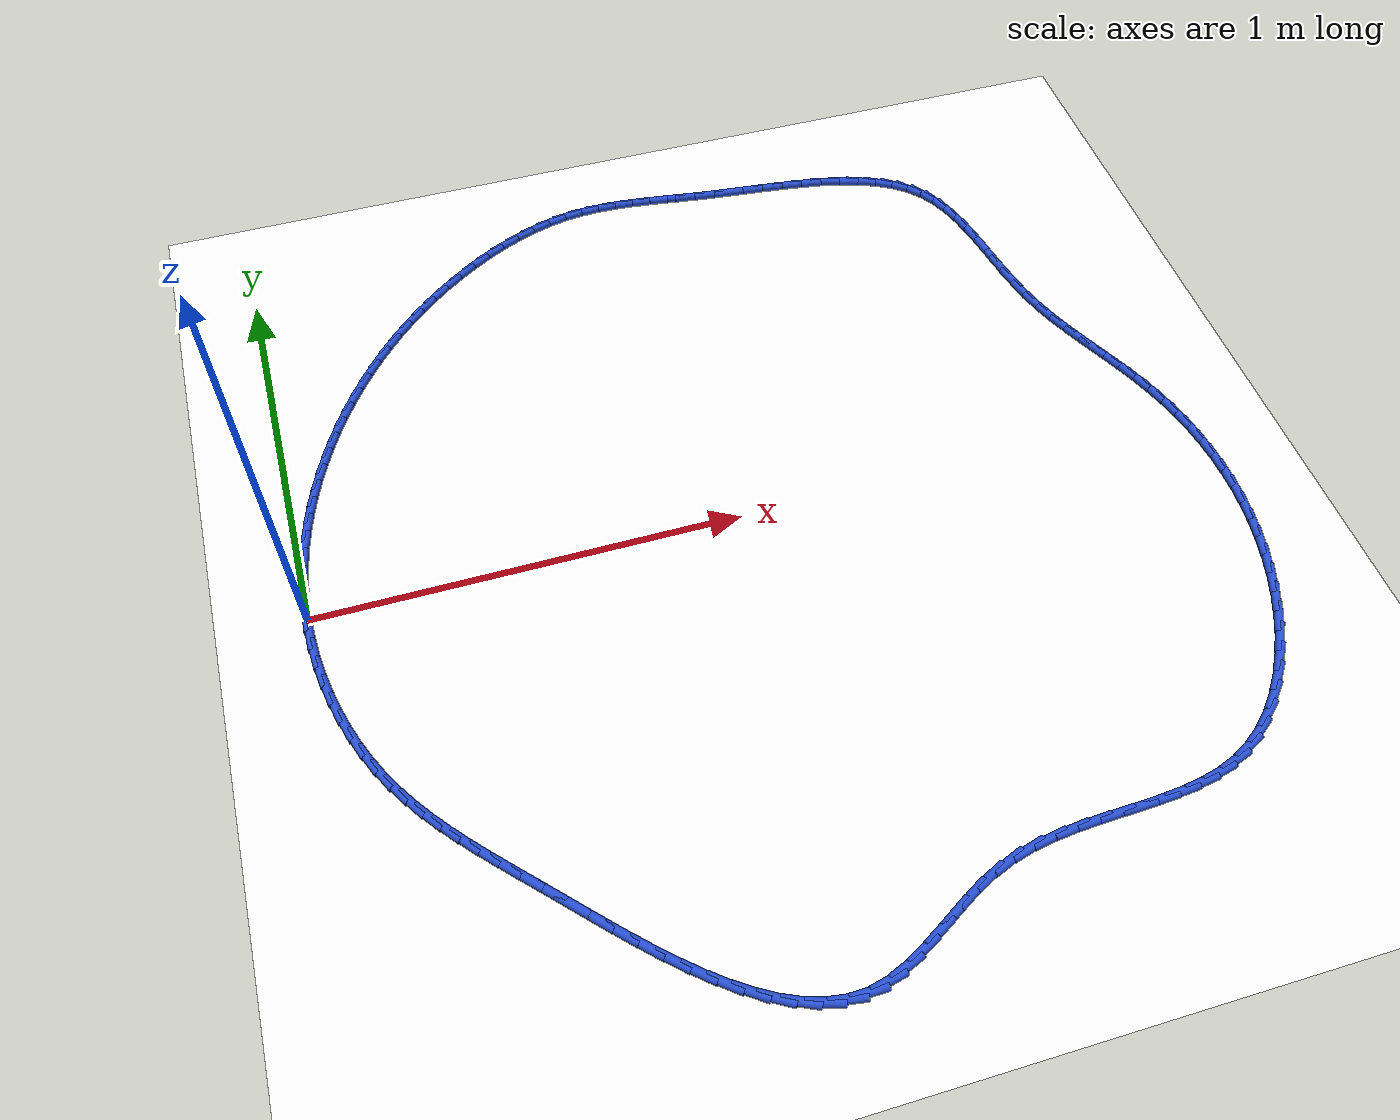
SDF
<sdf version="1.6">
 <world name="default">
  <light name="sun" type="directional">
   <pose>0 0 10 0 -0 0</pose>
   <diffuse>0.8 0.8 0.8 1</diffuse>
   <specular>0.2 0.2 0.2 1</specular>
   <attenuation>
    <range>1000</range>
    <constant>0.9</constant>
    <linear>0.01</linear>
    <quadratic>0.001</quadratic>
   </attenuation>
   <direction>-0.5 0.1 -0.9</direction>
  </light>
  <model name="ground_plane">
   <static>1</static>
   <link name="link">
    <collision name="collision">
     <geometry><plane><normal>0 0 1</normal><size>100 100</size></plane></geometry>
     <surface><friction><ode><mu>100</mu><mu2>50</mu2></ode></friction></surface>
    </collision>
    <visual name="visual">
     <cast_shadows>0</cast_shadows>
     <geometry><plane><normal>0 0 1</normal><size>100 100</size></plane></geometry>
     <material>
      <script><uri>file://media/materials/scripts/gazebo.material</uri><name>Gazebo/WhiteGlow</name></script>
     </material>
    </visual>
   </link>
  </model>
  <gravity>0 0 -9.8</gravity>
  <magnetic_field>6e-06 2.3e-05 -4.2e-05</magnetic_field>
  <atmosphere type="adiabatic"/>
  <physics name="default_physics" default="0" type="ode">
   <max_step_size>0.001</max_step_size>
   <real_time_factor>1</real_time_factor>
   <real_time_update_rate>1000</real_time_update_rate>
  </physics>
  <scene><ambient>0.4 0.4 0.4 1</ambient><background>0.7 0.7 0.7 1</background><shadows>1</shadows></scene>
  <spherical_coordinates>
   <surface_model>EARTH_WGS84</surface_model>
   <latitude_deg>0</latitude_deg>
   <longitude_deg>0</longitude_deg>
   <elevation>0</elevation>
   <heading_deg>0</heading_deg>
  </spherical_coordinates>
  <model name="line">
   <link name="link_0">
    <pose>-1.5612511283791264e-17 -1.5265566588595902e-16 0.01 0 1.57 1.5342450646788208</pose>
    <collision name="collision">
     <geometry><cylinder><radius>0.01</radius><length>0.08</length></cylinder></geometry>
    </collision>
    <visual name="visual">
     <material>
      <script><name>Gazebo/Blue</name><uri>file://media/materials/scripts/gazebo.material</uri></script>
     </material>
     <geometry><cylinder><radius>0.01</radius><length>0.08</length></cylinder></geometry>
    </visual>
   </link>
   <link name="link_1">
    <pose>0.0018194349702626465 0.049755454146792215 0.01 0 1.57 1.483602633361678</pose>
    <collision name="collision">
     <geometry><cylinder><radius>0.01</radius><length>0.08</length></cylinder></geometry>
    </collision>
    <visual name="visual">
     <material>
      <script><name>Gazebo/Blue</name><uri>file://media/materials/scripts/gazebo.material</uri></script>
     </material>
     <geometry><cylinder><radius>0.01</radius><length>0.08</length></cylinder></geometry>
    </visual>
   </link>
   <link name="link_2">
    <pose>0.006136728174320169 0.0991437344091996 0.01 0 1.57 1.4345923530516969</pose>
    <collision name="collision">
     <geometry><cylinder><radius>0.01</radius><length>0.08</length></cylinder></geometry>
    </collision>
    <visual name="visual">
     <material>
      <script><name>Gazebo/Blue</name><uri>file://media/materials/scripts/gazebo.material</uri></script>
     </material>
     <geometry><cylinder><radius>0.01</radius><length>0.08</length></cylinder></geometry>
    </visual>
   </link>
   <link name="link_3">
    <pose>0.012848926189753597 0.14811910012295137 0.01 0 1.57 1.3872954782884424</pose>
    <collision name="collision">
     <geometry><cylinder><radius>0.01</radius><length>0.08</length></cylinder></geometry>
    </collision>
    <visual name="visual">
     <material>
      <script><name>Gazebo/Blue</name><uri>file://media/materials/scripts/gazebo.material</uri></script>
     </material>
     <geometry><cylinder><radius>0.01</radius><length>0.08</length></cylinder></geometry>
    </visual>
   </link>
   <link name="link_4">
    <pose>0.021853075594143977 0.1966358106237768 0.01 0 1.57 1.341756516457929</pose>
    <collision name="collision">
     <geometry><cylinder><radius>0.01</radius><length>0.08</length></cylinder></geometry>
    </collision>
    <visual name="visual">
     <material>
      <script><name>Gazebo/Blue</name><uri>file://media/materials/scripts/gazebo.material</uri></script>
     </material>
     <geometry><cylinder><radius>0.01</radius><length>0.08</length></cylinder></geometry>
    </visual>
   </link>
   <link name="link_5">
    <pose>0.03304622296507237 0.2446481252474054 0.01 0 1.57 1.2979872696164079</pose>
    <collision name="collision">
     <geometry><cylinder><radius>0.01</radius><length>0.08</length></cylinder></geometry>
    </collision>
    <visual name="visual">
     <material>
      <script><name>Gazebo/Blue</name><uri>file://media/materials/scripts/gazebo.material</uri></script>
     </material>
     <geometry><cylinder><radius>0.01</radius><length>0.08</length></cylinder></geometry>
    </visual>
   </link>
   <link name="link_6">
    <pose>0.04632541488011981 0.29211030332956645 0.01 0 1.57 1.2559713870289138</pose>
    <collision name="collision">
     <geometry><cylinder><radius>0.01</radius><length>0.08</length></cylinder></geometry>
    </collision>
    <visual name="visual">
     <material>
      <script><name>Gazebo/Blue</name><uri>file://media/materials/scripts/gazebo.material</uri></script>
     </material>
     <geometry><cylinder><radius>0.01</radius><length>0.08</length></cylinder></geometry>
    </visual>
   </link>
   <link name="link_7">
    <pose>0.06158769791686734 0.3389766042059892 0.01 0 1.57 1.215669023698207</pose>
    <collision name="collision">
     <geometry><cylinder><radius>0.01</radius><length>0.08</length></cylinder></geometry>
    </collision>
    <visual name="visual">
     <material>
      <script><name>Gazebo/Blue</name><uri>file://media/materials/scripts/gazebo.material</uri></script>
     </material>
     <geometry><cylinder><radius>0.01</radius><length>0.08</length></cylinder></geometry>
    </visual>
   </link>
   <link name="link_8">
    <pose>0.07873011865289604 0.3852012872124031 0.01 0 1.57 1.17702129964449</pose>
    <collision name="collision">
     <geometry><cylinder><radius>0.01</radius><length>0.08</length></cylinder></geometry>
    </collision>
    <visual name="visual">
     <material>
      <script><name>Gazebo/Blue</name><uri>file://media/materials/scripts/gazebo.material</uri></script>
     </material>
     <geometry><cylinder><radius>0.01</radius><length>0.08</length></cylinder></geometry>
    </visual>
   </link>
   <link name="link_9">
    <pose>0.09764972366578695 0.4307386116845375 0.01 0 1.57 1.1397223946646875</pose>
    <collision name="collision">
     <geometry><cylinder><radius>0.01</radius><length>0.08</length></cylinder></geometry>
    </collision>
    <visual name="visual">
     <material>
      <script><name>Gazebo/Blue</name><uri>file://media/materials/scripts/gazebo.material</uri></script>
     </material>
     <geometry><cylinder><radius>0.01</radius><length>0.08</length></cylinder></geometry>
    </visual>
   </link>
   <link name="link_10">
    <pose>0.11825523203445562 0.47554084261589774 0.01 0 1.57 1.1025616992202147</pose>
    <collision name="collision">
     <geometry><cylinder><radius>0.01</radius><length>0.08</length></cylinder></geometry>
    </collision>
    <visual name="visual">
     <material>
      <script><name>Gazebo/Blue</name><uri>file://media/materials/scripts/gazebo.material</uri></script>
     </material>
     <geometry><cylinder><radius>0.01</radius><length>0.08</length></cylinder></geometry>
    </visual>
   </link>
   <link name="link_11">
    <pose>0.1405129374051986 0.519550407914736 0.01 0 1.57 1.0651474809801442</pose>
    <collision name="collision">
     <geometry><cylinder><radius>0.01</radius><length>0.08</length></cylinder></geometry>
    </collision>
    <visual name="visual">
     <material>
      <script><name>Gazebo/Blue</name><uri>file://media/materials/scripts/gazebo.material</uri></script>
     </material>
     <geometry><cylinder><radius>0.01</radius><length>0.08</length></cylinder></geometry>
    </visual>
   </link>
   <link name="link_12">
    <pose>0.16440685423022963 0.562706707744824 0.01 0 1.57 1.027445736495339</pose>
    <collision name="collision">
     <geometry><cylinder><radius>0.01</radius><length>0.08</length></cylinder></geometry>
    </collision>
    <visual name="visual">
     <material>
      <script><name>Gazebo/Blue</name><uri>file://media/materials/scripts/gazebo.material</uri></script>
     </material>
     <geometry><cylinder><radius>0.01</radius><length>0.08</length></cylinder></geometry>
    </visual>
   </link>
   <link name="link_13">
    <pose>0.18992100186058716 0.6049491414329298 0.01 0 1.57 0.9894254827330592</pose>
    <collision name="collision">
     <geometry><cylinder><radius>0.01</radius><length>0.08</length></cylinder></geometry>
    </collision>
    <visual name="visual">
     <material>
      <script><name>Gazebo/Blue</name><uri>file://media/materials/scripts/gazebo.material</uri></script>
     </material>
     <geometry><cylinder><radius>0.01</radius><length>0.08</length></cylinder></geometry>
    </visual>
   </link>
   <link name="link_14">
    <pose>0.21703939964730976 0.6462171083058211 0.01 0 1.57 0.951059174953108</pose>
    <collision name="collision">
     <geometry><cylinder><radius>0.01</radius><length>0.08</length></cylinder></geometry>
    </collision>
    <visual name="visual">
     <material>
      <script><name>Gazebo/Blue</name><uri>file://media/materials/scripts/gazebo.material</uri></script>
     </material>
     <geometry><cylinder><radius>0.01</radius><length>0.08</length></cylinder></geometry>
    </visual>
   </link>
   <link name="link_15">
    <pose>0.24574606694143597 0.686450007690266 0.01 0 1.57 0.9123232419840897</pose>
    <collision name="collision">
     <geometry><cylinder><radius>0.01</radius><length>0.08</length></cylinder></geometry>
    </collision>
    <visual name="visual">
     <material>
      <script><name>Gazebo/Blue</name><uri>file://media/materials/scripts/gazebo.material</uri></script>
     </material>
     <geometry><cylinder><radius>0.01</radius><length>0.08</length></cylinder></geometry>
    </visual>
   </link>
   <link name="link_16">
    <pose>0.27602502309400434 0.7255872389130321 0.01 0 1.57 0.8731986354613531</pose>
    <collision name="collision">
     <geometry><cylinder><radius>0.01</radius><length>0.08</length></cylinder></geometry>
    </collision>
    <visual name="visual">
     <material>
      <script><name>Gazebo/Blue</name><uri>file://media/materials/scripts/gazebo.material</uri></script>
     </material>
     <geometry><cylinder><radius>0.01</radius><length>0.08</length></cylinder></geometry>
    </visual>
   </link>
   <link name="link_17">
    <pose>0.3078602874560533 0.7635682013008875 0.01 0 1.57 0.8336713838829888</pose>
    <collision name="collision">
     <geometry><cylinder><radius>0.01</radius><length>0.08</length></cylinder></geometry>
    </collision>
    <visual name="visual">
     <material>
      <script><name>Gazebo/Blue</name><uri>file://media/materials/scripts/gazebo.material</uri></script>
     </material>
     <geometry><cylinder><radius>0.01</radius><length>0.08</length></cylinder></geometry>
    </visual>
   </link>
   <link name="link_18">
    <pose>0.3412358793786213 0.8003322941805997 0.01 0 1.57 0.7937331390714485</pose>
    <collision name="collision">
     <geometry><cylinder><radius>0.01</radius><length>0.08</length></cylinder></geometry>
    </collision>
    <visual name="visual">
     <material>
      <script><name>Gazebo/Blue</name><uri>file://media/materials/scripts/gazebo.material</uri></script>
     </material>
     <geometry><cylinder><radius>0.01</radius><length>0.08</length></cylinder></geometry>
    </visual>
   </link>
   <link name="link_19">
    <pose>0.376135818212747 0.8358189168789364 0.01 0 1.57 0.7533816992979713</pose>
    <collision name="collision">
     <geometry><cylinder><radius>0.01</radius><length>0.08</length></cylinder></geometry>
    </collision>
    <visual name="visual">
     <material>
      <script><name>Gazebo/Blue</name><uri>file://media/materials/scripts/gazebo.material</uri></script>
     </material>
     <geometry><cylinder><radius>0.01</radius><length>0.08</length></cylinder></geometry>
    </visual>
   </link>
   <link name="link_20">
    <pose>0.4125441233094689 0.8699674687226657 0.01 0 1.57 0.7126214901543351</pose>
    <collision name="collision">
     <geometry><cylinder><radius>0.01</radius><length>0.08</length></cylinder></geometry>
    </collision>
    <visual name="visual">
     <material>
      <script><name>Gazebo/Blue</name><uri>file://media/materials/scripts/gazebo.material</uri></script>
     </material>
     <geometry><cylinder><radius>0.01</radius><length>0.08</length></cylinder></geometry>
    </visual>
   </link>
   <link name="link_21">
    <pose>0.4504448140198256 0.9027173490385559 0.01 0 1.57 0.6714639815200801</pose>
    <collision name="collision">
     <geometry><cylinder><radius>0.01</radius><length>0.08</length></cylinder></geometry>
    </collision>
    <visual name="visual">
     <material>
      <script><name>Gazebo/Blue</name><uri>file://media/materials/scripts/gazebo.material</uri></script>
     </material>
     <geometry><cylinder><radius>0.01</radius><length>0.08</length></cylinder></geometry>
    </visual>
   </link>
   <link name="link_22">
    <pose>0.4898219096948555 0.9340079571533739 0.01 0 1.57 0.6299079099260075</pose>
    <collision name="collision">
     <geometry><cylinder><radius>0.01</radius><length>0.08</length></cylinder></geometry>
    </collision>
    <visual name="visual">
     <material>
      <script><name>Gazebo/Blue</name><uri>file://media/materials/scripts/gazebo.material</uri></script>
     </material>
     <geometry><cylinder><radius>0.01</radius><length>0.08</length></cylinder></geometry>
    </visual>
   </link>
   <link name="link_23">
    <pose>0.5306584268990399 0.9637767039003803 0.01 0 1.57 0.5866452012484016</pose>
    <collision name="collision">
     <geometry><cylinder><radius>0.01</radius><length>0.08</length></cylinder></geometry>
    </collision>
    <visual name="visual">
     <material>
      <script><name>Gazebo/Blue</name><uri>file://media/materials/scripts/gazebo.material</uri></script>
     </material>
     <geometry><cylinder><radius>0.01</radius><length>0.08</length></cylinder></geometry>
    </visual>
   </link>
   <link name="link_24">
    <pose>0.5728758259570633 0.9918389360680806 0.01 0 1.57 0.5391680719599047</pose>
    <collision name="collision">
     <geometry><cylinder><radius>0.01</radius><length>0.08</length></cylinder></geometry>
    </collision>
    <visual name="visual">
     <material>
      <script><name>Gazebo/Blue</name><uri>file://media/materials/scripts/gazebo.material</uri></script>
     </material>
     <geometry><cylinder><radius>0.01</radius><length>0.08</length></cylinder></geometry>
    </visual>
   </link>
   <link name="link_25">
    <pose>0.6162993476319881 1.0178192001473185 0.01 0 1.57 0.48647269864728404</pose>
    <collision name="collision">
     <geometry><cylinder><radius>0.01</radius><length>0.08</length></cylinder></geometry>
    </collision>
    <visual name="visual">
     <material>
      <script><name>Gazebo/Blue</name><uri>file://media/materials/scripts/gazebo.material</uri></script>
     </material>
     <geometry><cylinder><radius>0.01</radius><length>0.08</length></cylinder></geometry>
    </visual>
   </link>
   <link name="link_26">
    <pose>0.660745860645407 1.0413254411398276 0.01 0 1.57 0.42764175349862216</pose>
    <collision name="collision">
     <geometry><cylinder><radius>0.01</radius><length>0.08</length></cylinder></geometry>
    </collision>
    <visual name="visual">
     <material>
      <script><name>Gazebo/Blue</name><uri>file://media/materials/scripts/gazebo.material</uri></script>
     </material>
     <geometry><cylinder><radius>0.01</radius><length>0.08</length></cylinder></geometry>
    </visual>
   </link>
   <link name="link_27">
    <pose>0.7060322337189124 1.0619656040473429 0.01 0 1.57 0.36169408252615554</pose>
    <collision name="collision">
     <geometry><cylinder><radius>0.01</radius><length>0.08</length></cylinder></geometry>
    </collision>
    <visual name="visual">
     <material>
      <script><name>Gazebo/Blue</name><uri>file://media/materials/scripts/gazebo.material</uri></script>
     </material>
     <geometry><cylinder><radius>0.01</radius><length>0.08</length></cylinder></geometry>
    </visual>
   </link>
   <link name="link_28">
    <pose>0.7519753355740979 1.079347633871599 0.01 0 1.57 0.287634446819233</pose>
    <collision name="collision">
     <geometry><cylinder><radius>0.01</radius><length>0.08</length></cylinder></geometry>
    </collision>
    <visual name="visual">
     <material>
      <script><name>Gazebo/Blue</name><uri>file://media/materials/scripts/gazebo.material</uri></script>
     </material>
     <geometry><cylinder><radius>0.01</radius><length>0.08</length></cylinder></geometry>
    </visual>
   </link>
   <link name="link_29">
    <pose>0.7983920349325566 1.0930794756143307 0.01 0 1.57 0.20455269811188523</pose>
    <collision name="collision">
     <geometry><cylinder><radius>0.01</radius><length>0.08</length></cylinder></geometry>
    </collision>
    <visual name="visual">
     <material>
      <script><name>Gazebo/Blue</name><uri>file://media/materials/scripts/gazebo.material</uri></script>
     </material>
     <geometry><cylinder><radius>0.01</radius><length>0.08</length></cylinder></geometry>
    </visual>
   </link>
   <link name="link_30">
    <pose>0.845099200515881 1.1027690742772724 0.01 0 1.57 0.11411562553044557</pose>
    <collision name="collision">
     <geometry><cylinder><radius>0.01</radius><length>0.08</length></cylinder></geometry>
    </collision>
    <visual name="visual">
     <material>
      <script><name>Gazebo/Blue</name><uri>file://media/materials/scripts/gazebo.material</uri></script>
     </material>
     <geometry><cylinder><radius>0.01</radius><length>0.08</length></cylinder></geometry>
    </visual>
   </link>
   <link name="link_31">
    <pose>0.8919518312388062 1.1081390216261917 0.01 0 1.57 0.03157217377657766</pose>
    <collision name="collision">
     <geometry><cylinder><radius>0.01</radius><length>0.08</length></cylinder></geometry>
    </collision>
    <visual name="visual">
     <material>
      <script><name>Gazebo/Blue</name><uri>file://media/materials/scripts/gazebo.material</uri></script>
     </material>
     <geometry><cylinder><radius>0.01</radius><length>0.08</length></cylinder></geometry>
    </visual>
   </link>
   <link name="link_32">
    <pose>0.9390425144659821 1.1096262710576204 0.01 0 1.57 -0.035424630919001894</pose>
    <collision name="collision">
     <geometry><cylinder><radius>0.01</radius><length>0.08</length></cylinder></geometry>
    </collision>
    <visual name="visual">
     <material>
      <script><name>Gazebo/Blue</name><uri>file://media/materials/scripts/gazebo.material</uri></script>
     </material>
     <geometry><cylinder><radius>0.01</radius><length>0.08</length></cylinder></geometry>
    </visual>
   </link>
   <link name="link_33">
    <pose>0.9865551901999472 1.1079424476509945 0.01 0 1.57 -0.08588138279649331</pose>
    <collision name="collision">
     <geometry><cylinder><radius>0.01</radius><length>0.08</length></cylinder></geometry>
    </collision>
    <visual name="visual">
     <material>
      <script><name>Gazebo/Blue</name><uri>file://media/materials/scripts/gazebo.material</uri></script>
     </material>
     <geometry><cylinder><radius>0.01</radius><length>0.08</length></cylinder></geometry>
    </visual>
   </link>
   <link name="link_34">
    <pose>1.0346739887554683 1.103799748701083 0.01 0 1.57 -0.11983788856053237</pose>
    <collision name="collision">
     <geometry><cylinder><radius>0.01</radius><length>0.08</length></cylinder></geometry>
    </collision>
    <visual name="visual">
     <material>
      <script><name>Gazebo/Blue</name><uri>file://media/materials/scripts/gazebo.material</uri></script>
     </material>
     <geometry><cylinder><radius>0.01</radius><length>0.08</length></cylinder></geometry>
    </visual>
   </link>
   <link name="link_35">
    <pose>1.0835830404473121 1.097910371502654 0.01 0 1.57 -0.13791955061841746</pose>
    <collision name="collision">
     <geometry><cylinder><radius>0.01</radius><length>0.08</length></cylinder></geometry>
    </collision>
    <visual name="visual">
     <material>
      <script><name>Gazebo/Blue</name><uri>file://media/materials/scripts/gazebo.material</uri></script>
     </material>
     <geometry><cylinder><radius>0.01</radius><length>0.08</length></cylinder></geometry>
    </visual>
   </link>
   <link name="link_36">
    <pose>1.1334664755902453 1.0909865133504753 0.01 0 1.57 -0.14102209893917067</pose>
    <collision name="collision">
     <geometry><cylinder><radius>0.01</radius><length>0.08</length></cylinder></geometry>
    </collision>
    <visual name="visual">
     <material>
      <script><name>Gazebo/Blue</name><uri>file://media/materials/scripts/gazebo.material</uri></script>
     </material>
     <geometry><cylinder><radius>0.01</radius><length>0.08</length></cylinder></geometry>
    </visual>
   </link>
   <link name="link_37">
    <pose>1.1845084244990347 1.0837403715393152 0.01 0 1.57 -0.13015006558396924</pose>
    <collision name="collision">
     <geometry><cylinder><radius>0.01</radius><length>0.08</length></cylinder></geometry>
    </collision>
    <visual name="visual">
     <material>
      <script><name>Gazebo/Blue</name><uri>file://media/materials/scripts/gazebo.material</uri></script>
     </material>
     <geometry><cylinder><radius>0.01</radius><length>0.08</length></cylinder></geometry>
    </visual>
   </link>
   <link name="link_38">
    <pose>1.2368927880006957 1.076883784739022 0.01 0 1.57 -0.11209958004925503</pose>
    <collision name="collision">
     <geometry><cylinder><radius>0.01</radius><length>0.08</length></cylinder></geometry>
    </collision>
    <visual name="visual">
     <material>
      <script><name>Gazebo/Blue</name><uri>file://media/materials/scripts/gazebo.material</uri></script>
     </material>
     <geometry><cylinder><radius>0.01</radius><length>0.08</length></cylinder></geometry>
    </visual>
   </link>
   <link name="link_39">
    <pose>1.2906162674651203 1.0708360514287223 0.01 0 1.57 -0.10306394920933935</pose>
    <collision name="collision">
     <geometry><cylinder><radius>0.01</radius><length>0.08</length></cylinder></geometry>
    </collision>
    <visual name="visual">
     <material>
      <script><name>Gazebo/Blue</name><uri>file://media/materials/scripts/gazebo.material</uri></script>
     </material>
     <geometry><cylinder><radius>0.01</radius><length>0.08</length></cylinder></geometry>
    </visual>
   </link>
   <link name="link_40">
    <pose>1.3451502661486434 1.0651955766261825 0.01 0 1.57 -0.10518876523561257</pose>
    <collision name="collision">
     <geometry><cylinder><radius>0.01</radius><length>0.08</length></cylinder></geometry>
    </collision>
    <visual name="visual">
     <material>
      <script><name>Gazebo/Blue</name><uri>file://media/materials/scripts/gazebo.material</uri></script>
     </material>
     <geometry><cylinder><radius>0.01</radius><length>0.08</length></cylinder></geometry>
    </visual>
   </link>
   <link name="link_41">
    <pose>1.3998747355774677 1.0594178519722455 0.01 0 1.57 -0.1184137800177648</pose>
    <collision name="collision">
     <geometry><cylinder><radius>0.01</radius><length>0.08</length></cylinder></geometry>
    </collision>
    <visual name="visual">
     <material>
      <script><name>Gazebo/Blue</name><uri>file://media/materials/scripts/gazebo.material</uri></script>
     </material>
     <geometry><cylinder><radius>0.01</radius><length>0.08</length></cylinder></geometry>
    </visual>
   </link>
   <link name="link_42">
    <pose>1.4541696272777922 1.0529583691077546 0.01 0 1.57 -0.14335598295028892</pose>
    <collision name="collision">
     <geometry><cylinder><radius>0.01</radius><length>0.08</length></cylinder></geometry>
    </collision>
    <visual name="visual">
     <material>
      <script><name>Gazebo/Blue</name><uri>file://media/materials/scripts/gazebo.material</uri></script>
     </material>
     <geometry><cylinder><radius>0.01</radius><length>0.08</length></cylinder></geometry>
    </visual>
   </link>
   <link name="link_43">
    <pose>1.5074148927758175 1.0452726196735527 0.01 0 1.57 -0.18133852121102176</pose>
    <collision name="collision">
     <geometry><cylinder><radius>0.01</radius><length>0.08</length></cylinder></geometry>
    </collision>
    <visual name="visual">
     <material>
      <script><name>Gazebo/Blue</name><uri>file://media/materials/scripts/gazebo.material</uri></script>
     </material>
     <geometry><cylinder><radius>0.01</radius><length>0.08</length></cylinder></geometry>
    </visual>
   </link>
   <link name="link_44">
    <pose>1.5589904835977457 1.0358160953104836 0.01 0 1.57 -0.23445499094795766</pose>
    <collision name="collision">
     <geometry><cylinder><radius>0.01</radius><length>0.08</length></cylinder></geometry>
    </collision>
    <visual name="visual">
     <material>
      <script><name>Gazebo/Blue</name><uri>file://media/materials/scripts/gazebo.material</uri></script>
     </material>
     <geometry><cylinder><radius>0.01</radius><length>0.08</length></cylinder></geometry>
    </visual>
   </link>
   <link name="link_45">
    <pose>1.6082763512697755 1.0240442876593898 0.01 0 1.57 -0.30561446821415944</pose>
    <collision name="collision">
     <geometry><cylinder><radius>0.01</radius><length>0.08</length></cylinder></geometry>
    </collision>
    <visual name="visual">
     <material>
      <script><name>Gazebo/Blue</name><uri>file://media/materials/scripts/gazebo.material</uri></script>
     </material>
     <geometry><cylinder><radius>0.01</radius><length>0.08</length></cylinder></geometry>
    </visual>
   </link>
   <link name="link_46">
    <pose>1.6546524473181086 1.0094126883611152 0.01 0 1.57 -0.3984304966839086</pose>
    <collision name="collision">
     <geometry><cylinder><radius>0.01</radius><length>0.08</length></cylinder></geometry>
    </collision>
    <visual name="visual">
     <material>
      <script><name>Gazebo/Blue</name><uri>file://media/materials/scripts/gazebo.material</uri></script>
     </material>
     <geometry><cylinder><radius>0.01</radius><length>0.08</length></cylinder></geometry>
    </visual>
   </link>
   <link name="link_47">
    <pose>1.6974987232689447 0.9913767890565026 0.01 0 1.57 -0.516658266013193</pose>
    <collision name="collision">
     <geometry><cylinder><radius>0.01</radius><length>0.08</length></cylinder></geometry>
    </collision>
    <visual name="visual">
     <material>
      <script><name>Gazebo/Blue</name><uri>file://media/materials/scripts/gazebo.material</uri></script>
     </material>
     <geometry><cylinder><radius>0.01</radius><length>0.08</length></cylinder></geometry>
    </visual>
   </link>
   <link name="link_48">
    <pose>1.7361951306484844 0.9693920813863948 0.01 0 1.57 -0.6627077543794281</pose>
    <collision name="collision">
     <geometry><cylinder><radius>0.01</radius><length>0.08</length></cylinder></geometry>
    </collision>
    <visual name="visual">
     <material>
      <script><name>Gazebo/Blue</name><uri>file://media/materials/scripts/gazebo.material</uri></script>
     </material>
     <geometry><cylinder><radius>0.01</radius><length>0.08</length></cylinder></geometry>
    </visual>
   </link>
   <link name="link_49">
    <pose>1.7701216209829285 0.9429140569916358 0.01 0 1.57 -0.8349144943348729</pose>
    <collision name="collision">
     <geometry><cylinder><radius>0.01</radius><length>0.08</length></cylinder></geometry>
    </collision>
    <visual name="visual">
     <material>
      <script><name>Gazebo/Blue</name><uri>file://media/materials/scripts/gazebo.material</uri></script>
     </material>
     <geometry><cylinder><radius>0.01</radius><length>0.08</length></cylinder></geometry>
    </visual>
   </link>
   <link name="link_50">
    <pose>1.798659930465634 0.911399728550578 0.01 0 1.57 -1.0119823204613876</pose>
    <collision name="collision">
     <geometry><cylinder><radius>0.01</radius><length>0.08</length></cylinder></geometry>
    </collision>
    <visual name="visual">
     <material>
      <script><name>Gazebo/Blue</name><uri>file://media/materials/scripts/gazebo.material</uri></script>
     </material>
     <geometry><cylinder><radius>0.01</radius><length>0.08</length></cylinder></geometry>
    </visual>
   </link>
   <link name="link_51">
    <pose>1.821624120006522 0.8746745707867749 0.01 0 1.57 -1.1554727165125553</pose>
    <collision name="collision">
     <geometry><cylinder><radius>0.01</radius><length>0.08</length></cylinder></geometry>
    </collision>
    <visual name="visual">
     <material>
      <script><name>Gazebo/Blue</name><uri>file://media/materials/scripts/gazebo.material</uri></script>
     </material>
     <geometry><cylinder><radius>0.01</radius><length>0.08</length></cylinder></geometry>
    </visual>
   </link>
   <link name="link_52">
    <pose>1.8398207835432094 0.8334099752434747 0.01 0 1.57 -1.26170079862764</pose>
    <collision name="collision">
     <geometry><cylinder><radius>0.01</radius><length>0.08</length></cylinder></geometry>
    </collision>
    <visual name="visual">
     <material>
      <script><name>Gazebo/Blue</name><uri>file://media/materials/scripts/gazebo.material</uri></script>
     </material>
     <geometry><cylinder><radius>0.01</radius><length>0.08</length></cylinder></geometry>
    </visual>
   </link>
   <link name="link_53">
    <pose>1.8541952541192648 0.7883955781368996 0.01 0 1.57 -1.3355723208216845</pose>
    <collision name="collision">
     <geometry><cylinder><radius>0.01</radius><length>0.08</length></cylinder></geometry>
    </collision>
    <visual name="visual">
     <material>
      <script><name>Gazebo/Blue</name><uri>file://media/materials/scripts/gazebo.material</uri></script>
     </material>
     <geometry><cylinder><radius>0.01</radius><length>0.08</length></cylinder></geometry>
    </visual>
   </link>
   <link name="link_54">
    <pose>1.865692864778256 0.740421015683271 0.01 0 1.57 -1.3822931482762668</pose>
    <collision name="collision">
     <geometry><cylinder><radius>0.01</radius><length>0.08</length></cylinder></geometry>
    </collision>
    <visual name="visual">
     <material>
      <script><name>Gazebo/Blue</name><uri>file://media/materials/scripts/gazebo.material</uri></script>
     </material>
     <geometry><cylinder><radius>0.01</radius><length>0.08</length></cylinder></geometry>
    </visual>
   </link>
   <link name="link_55">
    <pose>1.8752589485637536 0.6902759240988106 0.01 0 1.57 -1.4057944530006135</pose>
    <collision name="collision">
     <geometry><cylinder><radius>0.01</radius><length>0.08</length></cylinder></geometry>
    </collision>
    <visual name="visual">
     <material>
      <script><name>Gazebo/Blue</name><uri>file://media/materials/scripts/gazebo.material</uri></script>
     </material>
     <geometry><cylinder><radius>0.01</radius><length>0.08</length></cylinder></geometry>
    </visual>
   </link>
   <link name="link_56">
    <pose>1.8838388385193252 0.638749939599741 0.01 0 1.57 -1.4083965509822691</pose>
    <collision name="collision">
     <geometry><cylinder><radius>0.01</radius><length>0.08</length></cylinder></geometry>
    </collision>
    <visual name="visual">
     <material>
      <script><name>Gazebo/Blue</name><uri>file://media/materials/scripts/gazebo.material</uri></script>
     </material>
     <geometry><cylinder><radius>0.01</radius><length>0.08</length></cylinder></geometry>
    </visual>
   </link>
   <link name="link_57">
    <pose>1.8923778676885405 0.5866326984022835 0.01 0 1.57 -1.3908736868109741</pose>
    <collision name="collision">
     <geometry><cylinder><radius>0.01</radius><length>0.08</length></cylinder></geometry>
    </collision>
    <visual name="visual">
     <material>
      <script><name>Gazebo/Blue</name><uri>file://media/materials/scripts/gazebo.material</uri></script>
     </material>
     <geometry><cylinder><radius>0.01</radius><length>0.08</length></cylinder></geometry>
    </visual>
   </link>
   <link name="link_58">
    <pose>1.901821369114968 0.5347138367226606 0.01 0 1.57 -1.3525888109360276</pose>
    <collision name="collision">
     <geometry><cylinder><radius>0.01</radius><length>0.08</length></cylinder></geometry>
    </collision>
    <visual name="visual">
     <material>
      <script><name>Gazebo/Blue</name><uri>file://media/materials/scripts/gazebo.material</uri></script>
     </material>
     <geometry><cylinder><radius>0.01</radius><length>0.08</length></cylinder></geometry>
    </visual>
   </link>
   <link name="link_59">
    <pose>1.9131146758421773 0.48378299077709386 0.01 0 1.57 -1.2935251363217228</pose>
    <collision name="collision">
     <geometry><cylinder><radius>0.01</radius><length>0.08</length></cylinder></geometry>
    </collision>
    <visual name="visual">
     <material>
      <script><name>Gazebo/Blue</name><uri>file://media/materials/scripts/gazebo.material</uri></script>
     </material>
     <geometry><cylinder><radius>0.01</radius><length>0.08</length></cylinder></geometry>
    </visual>
   </link>
   <link name="link_60">
    <pose>1.9271207796067409 0.43457007391937036 0.01 0 1.57 -1.2330121913697736</pose>
    <collision name="collision">
     <geometry><cylinder><radius>0.01</radius><length>0.08</length></cylinder></geometry>
    </collision>
    <visual name="visual">
     <material>
      <script><name>Gazebo/Blue</name><uri>file://media/materials/scripts/gazebo.material</uri></script>
     </material>
     <geometry><cylinder><radius>0.01</radius><length>0.08</length></cylinder></geometry>
    </visual>
   </link>
   <link name="link_61">
    <pose>1.9437814918213707 0.3871368594437208 0.01 0 1.57 -1.1851440554485118</pose>
    <collision name="collision">
     <geometry><cylinder><radius>0.01</radius><length>0.08</length></cylinder></geometry>
    </collision>
    <visual name="visual">
     <material>
      <script><name>Gazebo/Blue</name><uri>file://media/materials/scripts/gazebo.material</uri></script>
     </material>
     <geometry><cylinder><radius>0.01</radius><length>0.08</length></cylinder></geometry>
    </visual>
   </link>
   <link name="link_62">
    <pose>1.9624609901621886 0.34112615789716233 0.01 0 1.57 -1.1511803039369946</pose>
    <collision name="collision">
     <geometry><cylinder><radius>0.01</radius><length>0.08</length></cylinder></geometry>
    </collision>
    <visual name="visual">
     <material>
      <script><name>Gazebo/Blue</name><uri>file://media/materials/scripts/gazebo.material</uri></script>
     </material>
     <geometry><cylinder><radius>0.01</radius><length>0.08</length></cylinder></geometry>
    </visual>
   </link>
   <link name="link_63">
    <pose>1.9825145473095374 0.2961743209562179 0.01 0 1.57 -1.1317634952829647</pose>
    <collision name="collision">
     <geometry><cylinder><radius>0.01</radius><length>0.08</length></cylinder></geometry>
    </collision>
    <visual name="visual">
     <material>
      <script><name>Gazebo/Blue</name><uri>file://media/materials/scripts/gazebo.material</uri></script>
     </material>
     <geometry><cylinder><radius>0.01</radius><length>0.08</length></cylinder></geometry>
    </visual>
   </link>
   <link name="link_64">
    <pose>2.003297435943758 0.25191770029741223 0.01 0 1.57 -1.1272905435924727</pose>
    <collision name="collision">
     <geometry><cylinder><radius>0.01</radius><length>0.08</length></cylinder></geometry>
    </collision>
    <visual name="visual">
     <material>
      <script><name>Gazebo/Blue</name><uri>file://media/materials/scripts/gazebo.material</uri></script>
     </material>
     <geometry><cylinder><radius>0.01</radius><length>0.08</length></cylinder></geometry>
    </visual>
   </link>
   <link name="link_65">
    <pose>2.0241649287451904 0.2079926475972686 0.01 0 1.57 -1.1380236128151178</pose>
    <collision name="collision">
     <geometry><cylinder><radius>0.01</radius><length>0.08</length></cylinder></geometry>
    </collision>
    <visual name="visual">
     <material>
      <script><name>Gazebo/Blue</name><uri>file://media/materials/scripts/gazebo.material</uri></script>
     </material>
     <geometry><cylinder><radius>0.01</radius><length>0.08</length></cylinder></geometry>
    </visual>
   </link>
   <link name="link_66">
    <pose>2.0444722983941777 0.1640355145323107 0.01 0 1.57 -1.1641125654377675</pose>
    <collision name="collision">
     <geometry><cylinder><radius>0.01</radius><length>0.08</length></cylinder></geometry>
    </collision>
    <visual name="visual">
     <material>
      <script><name>Gazebo/Blue</name><uri>file://media/materials/scripts/gazebo.material</uri></script>
     </material>
     <geometry><cylinder><radius>0.01</radius><length>0.08</length></cylinder></geometry>
    </visual>
   </link>
   <link name="link_67">
    <pose>2.063574817571059 0.11968265277906295 0.01 0 1.57 -1.2055146921717141</pose>
    <collision name="collision">
     <geometry><cylinder><radius>0.01</radius><length>0.08</length></cylinder></geometry>
    </collision>
    <visual name="visual">
     <material>
      <script><name>Gazebo/Blue</name><uri>file://media/materials/scripts/gazebo.material</uri></script>
     </material>
     <geometry><cylinder><radius>0.01</radius><length>0.08</length></cylinder></geometry>
    </visual>
   </link>
   <link name="link_68">
    <pose>2.08082776053113 0.07457041529166024 0.01 0 1.57 -1.2590917931281338</pose>
    <collision name="collision">
     <geometry><cylinder><radius>0.01</radius><length>0.08</length></cylinder></geometry>
    </collision>
    <visual name="visual">
     <material>
      <script><name>Gazebo/Blue</name><uri>file://media/materials/scripts/gazebo.material</uri></script>
     </material>
     <geometry><cylinder><radius>0.01</radius><length>0.08</length></cylinder></geometry>
    </visual>
   </link>
   <link name="link_69">
    <pose>2.095696383156413 0.028424372813559154 0.01 0 1.57 -1.3143252042439373</pose>
    <collision name="collision">
     <geometry><cylinder><radius>0.01</radius><length>0.08</length></cylinder></geometry>
    </collision>
    <visual name="visual">
     <material>
      <script><name>Gazebo/Blue</name><uri>file://media/materials/scripts/gazebo.material</uri></script>
     </material>
     <geometry><cylinder><radius>0.01</radius><length>0.08</length></cylinder></geometry>
    </visual>
   </link>
   <link name="link_70">
    <pose>2.108054239630774 -0.018698689753959268 0.01 0 1.57 -1.3689528828809112</pose>
    <collision name="collision">
     <geometry><cylinder><radius>0.01</radius><length>0.08</length></cylinder></geometry>
    </collision>
    <visual name="visual">
     <material>
      <script><name>Gazebo/Blue</name><uri>file://media/materials/scripts/gazebo.material</uri></script>
     </material>
     <geometry><cylinder><radius>0.01</radius><length>0.08</length></cylinder></geometry>
    </visual>
   </link>
   <link name="link_71">
    <pose>2.1178696125427465 -0.0666651432302403 0.01 0 1.57 -1.4231173401517498</pose>
    <collision name="collision">
     <geometry><cylinder><radius>0.01</radius><length>0.08</length></cylinder></geometry>
    </collision>
    <visual name="visual">
     <material>
      <script><name>Gazebo/Blue</name><uri>file://media/materials/scripts/gazebo.material</uri></script>
     </material>
     <geometry><cylinder><radius>0.01</radius><length>0.08</length></cylinder></geometry>
    </visual>
   </link>
   <link name="link_72">
    <pose>2.125110784480862 -0.11534135843463025 0.01 0 1.57 -1.4769603775398468</pose>
    <collision name="collision">
     <geometry><cylinder><radius>0.01</radius><length>0.08</length></cylinder></geometry>
    </collision>
    <visual name="visual">
     <material>
      <script><name>Gazebo/Blue</name><uri>file://media/materials/scripts/gazebo.material</uri></script>
     </material>
     <geometry><cylinder><radius>0.01</radius><length>0.08</length></cylinder></geometry>
    </visual>
   </link>
   <link name="link_73">
    <pose>2.1297460380336526 -0.16459370618647606 0.01 0 1.57 -1.5306202763503305</pose>
    <collision name="collision">
     <geometry><cylinder><radius>0.01</radius><length>0.08</length></cylinder></geometry>
    </collision>
    <visual name="visual">
     <material>
      <script><name>Gazebo/Blue</name><uri>file://media/materials/scripts/gazebo.material</uri></script>
     </material>
     <geometry><cylinder><radius>0.01</radius><length>0.08</length></cylinder></geometry>
    </visual>
   </link>
   <link name="link_74">
    <pose>2.131743655789652 -0.21428855730512217 0.01 0 1.57 1.5573634266578944</pose>
    <collision name="collision">
     <geometry><cylinder><radius>0.01</radius><length>0.08</length></cylinder></geometry>
    </collision>
    <visual name="visual">
     <material>
      <script><name>Gazebo/Blue</name><uri>file://media/materials/scripts/gazebo.material</uri></script>
     </material>
     <geometry><cylinder><radius>0.01</radius><length>0.08</length></cylinder></geometry>
    </visual>
   </link>
   <link name="link_75">
    <pose>2.131071920337392 -0.26429228260991533 0.01 0 1.57 1.5036817484877711</pose>
    <collision name="collision">
     <geometry><cylinder><radius>0.01</radius><length>0.08</length></cylinder></geometry>
    </collision>
    <visual name="visual">
     <material>
      <script><name>Gazebo/Blue</name><uri>file://media/materials/scripts/gazebo.material</uri></script>
     </material>
     <geometry><cylinder><radius>0.01</radius><length>0.08</length></cylinder></geometry>
    </visual>
   </link>
   <link name="link_76">
    <pose>2.1276991142654054 -0.31447125292020156 0.01 0 1.57 1.4498145323759668</pose>
    <collision name="collision">
     <geometry><cylinder><radius>0.01</radius><length>0.08</length></cylinder></geometry>
    </collision>
    <visual name="visual">
     <material>
      <script><name>Gazebo/Blue</name><uri>file://media/materials/scripts/gazebo.material</uri></script>
     </material>
     <geometry><cylinder><radius>0.01</radius><length>0.08</length></cylinder></geometry>
    </visual>
   </link>
   <link name="link_77">
    <pose>2.1215935201622242 -0.3646918390553269 0.01 0 1.57 1.3956621617604974</pose>
    <collision name="collision">
     <geometry><cylinder><radius>0.01</radius><length>0.08</length></cylinder></geometry>
    </collision>
    <visual name="visual">
     <material>
      <script><name>Gazebo/Blue</name><uri>file://media/materials/scripts/gazebo.material</uri></script>
     </material>
     <geometry><cylinder><radius>0.01</radius><length>0.08</length></cylinder></geometry>
    </visual>
   </link>
   <link name="link_78">
    <pose>2.112723420616382 -0.41482041183463825 0.01 0 1.57 1.3411405396196014</pose>
    <collision name="collision">
     <geometry><cylinder><radius>0.01</radius><length>0.08</length></cylinder></geometry>
    </collision>
    <visual name="visual">
     <material>
      <script><name>Gazebo/Blue</name><uri>file://media/materials/scripts/gazebo.material</uri></script>
     </material>
     <geometry><cylinder><radius>0.01</radius><length>0.08</length></cylinder></geometry>
    </visual>
   </link>
   <link name="link_79">
    <pose>2.10105709821641 -0.4647233420774799 0.01 0 1.57 1.2861833971301648</pose>
    <collision name="collision">
     <geometry><cylinder><radius>0.01</radius><length>0.08</length></cylinder></geometry>
    </collision>
    <visual name="visual">
     <material>
      <script><name>Gazebo/Blue</name><uri>file://media/materials/scripts/gazebo.material</uri></script>
     </material>
     <geometry><cylinder><radius>0.01</radius><length>0.08</length></cylinder></geometry>
    </visual>
   </link>
   <link name="link_80">
    <pose>2.086562835550841 -0.5142670006031989 0.01 0 1.57 1.2307445329764355</pose>
    <collision name="collision">
     <geometry><cylinder><radius>0.01</radius><length>0.08</length></cylinder></geometry>
    </collision>
    <visual name="visual">
     <material>
      <script><name>Gazebo/Blue</name><uri>file://media/materials/scripts/gazebo.material</uri></script>
     </material>
     <geometry><cylinder><radius>0.01</radius><length>0.08</length></cylinder></geometry>
    </visual>
   </link>
   <link name="link_81">
    <pose>2.0692089152082085 -0.5633177582311408 0.01 0 1.57 1.1745458936774877</pose>
    <collision name="collision">
     <geometry><cylinder><radius>0.01</radius><length>0.08</length></cylinder></geometry>
    </collision>
    <visual name="visual">
     <material>
      <script><name>Gazebo/Blue</name><uri>file://media/materials/scripts/gazebo.material</uri></script>
     </material>
     <geometry><cylinder><radius>0.01</radius><length>0.08</length></cylinder></geometry>
    </visual>
   </link>
   <link name="link_82">
    <pose>2.048973559353471 -0.6116836878947159 0.01 0 1.57 1.115618686900558</pose>
    <collision name="collision">
     <geometry><cylinder><radius>0.01</radius><length>0.08</length></cylinder></geometry>
    </collision>
    <visual name="visual">
     <material>
      <script><name>Gazebo/Blue</name><uri>file://media/materials/scripts/gazebo.material</uri></script>
     </material>
     <geometry><cylinder><radius>0.01</radius><length>0.08</length></cylinder></geometry>
    </visual>
   </link>
   <link name="link_83">
    <pose>2.025891296559263 -0.6588426125860004 0.01 0 1.57 1.051960383859258</pose>
    <collision name="collision">
     <geometry><cylinder><radius>0.01</radius><length>0.08</length></cylinder></geometry>
    </collision>
    <visual name="visual">
     <material>
      <script><name>Gazebo/Blue</name><uri>file://media/materials/scripts/gazebo.material</uri></script>
     </material>
     <geometry><cylinder><radius>0.01</radius><length>0.08</length></cylinder></geometry>
    </visual>
   </link>
   <link name="link_84">
    <pose>2.000016459606581 -0.7041561990917599 0.01 0 1.57 0.9818266752228897</pose>
    <collision name="collision">
     <geometry><cylinder><radius>0.01</radius><length>0.08</length></cylinder></geometry>
    </collision>
    <visual name="visual">
     <material>
      <script><name>Gazebo/Blue</name><uri>file://media/materials/scripts/gazebo.material</uri></script>
     </material>
     <geometry><cylinder><radius>0.01</radius><length>0.08</length></cylinder></geometry>
    </visual>
   </link>
   <link name="link_85">
    <pose>1.9714034031608327 -0.746985985841685 0.01 0 1.57 0.9033005835065494</pose>
    <collision name="collision">
     <geometry><cylinder><radius>0.01</radius><length>0.08</length></cylinder></geometry>
    </collision>
    <visual name="visual">
     <material>
      <script><name>Gazebo/Blue</name><uri>file://media/materials/scripts/gazebo.material</uri></script>
     </material>
     <geometry><cylinder><radius>0.01</radius><length>0.08</length></cylinder></geometry>
    </visual>
   </link>
   <link name="link_86">
    <pose>1.940106481887428 -0.7866935112654678 0.01 0 1.57 0.8143049164532797</pose>
    <collision name="collision">
     <geometry><cylinder><radius>0.01</radius><length>0.08</length></cylinder></geometry>
    </collision>
    <visual name="visual">
     <material>
      <script><name>Gazebo/Blue</name><uri>file://media/materials/scripts/gazebo.material</uri></script>
     </material>
     <geometry><cylinder><radius>0.01</radius><length>0.08</length></cylinder></geometry>
    </visual>
   </link>
   <link name="link_87">
    <pose>1.906180050451773 -0.8226403137927997 0.01 0 1.57 0.7127265591327666</pose>
    <collision name="collision">
     <geometry><cylinder><radius>0.01</radius><length>0.08</length></cylinder></geometry>
    </collision>
    <visual name="visual">
     <material>
      <script><name>Gazebo/Blue</name><uri>file://media/materials/scripts/gazebo.material</uri></script>
     </material>
     <geometry><cylinder><radius>0.01</radius><length>0.08</length></cylinder></geometry>
    </visual>
   </link>
   <link name="link_88">
    <pose>1.869678463519279 -0.8541879318533709 0.01 0 1.57 0.5967340284299513</pose>
    <collision name="collision">
     <geometry><cylinder><radius>0.01</radius><length>0.08</length></cylinder></geometry>
    </collision>
    <visual name="visual">
     <material>
      <script><name>Gazebo/Blue</name><uri>file://media/materials/scripts/gazebo.material</uri></script>
     </material>
     <geometry><cylinder><radius>0.01</radius><length>0.08</length></cylinder></geometry>
    </visual>
   </link>
   <link name="link_89">
    <pose>1.8306560757553525 -0.8806979038768736 0.01 0 1.57 0.4655902658144307</pose>
    <collision name="collision">
     <geometry><cylinder><radius>0.01</radius><length>0.08</length></cylinder></geometry>
    </collision>
    <visual name="visual">
     <material>
      <script><name>Gazebo/Blue</name><uri>file://media/materials/scripts/gazebo.material</uri></script>
     </material>
     <geometry><cylinder><radius>0.01</radius><length>0.08</length></cylinder></geometry>
    </visual>
   </link>
   <link name="link_90">
    <pose>1.789169011243359 -0.901542278121104 0.01 0 1.57 0.33341469124790507</pose>
    <collision name="collision">
     <geometry><cylinder><radius>0.01</radius><length>0.08</length></cylinder></geometry>
    </collision>
    <visual name="visual">
     <material>
      <script><name>Gazebo/Blue</name><uri>file://media/materials/scripts/gazebo.material</uri></script>
     </material>
     <geometry><cylinder><radius>0.01</radius><length>0.08</length></cylinder></geometry>
    </visual>
   </link>
   <link name="link_91">
    <pose>1.745377145653748 -0.9167093570997585 0.01 0 1.57 0.22391660037434966</pose>
    <collision name="collision">
     <geometry><cylinder><radius>0.01</radius><length>0.08</length></cylinder></geometry>
    </collision>
    <visual name="visual">
     <material>
      <script><name>Gazebo/Blue</name><uri>file://media/materials/scripts/gazebo.material</uri></script>
     </material>
     <geometry><cylinder><radius>0.01</radius><length>0.08</length></cylinder></geometry>
    </visual>
   </link>
   <link name="link_92">
    <pose>1.6995997970013939 -0.9271344844859123 0.01 0 1.57 0.14031257284140733</pose>
    <collision name="collision">
     <geometry><cylinder><radius>0.01</radius><length>0.08</length></cylinder></geometry>
    </collision>
    <visual name="visual">
     <material>
      <script><name>Gazebo/Blue</name><uri>file://media/materials/scripts/gazebo.material</uri></script>
     </material>
     <geometry><cylinder><radius>0.01</radius><length>0.08</length></cylinder></geometry>
    </visual>
   </link>
   <link name="link_93">
    <pose>1.652169839589459 -0.9338335243628557 0.01 0 1.57 0.08164052539482167</pose>
    <collision name="collision">
     <geometry><cylinder><radius>0.01</radius><length>0.08</length></cylinder></geometry>
    </collision>
    <visual name="visual">
     <material>
      <script><name>Gazebo/Blue</name><uri>file://media/materials/scripts/gazebo.material</uri></script>
     </material>
     <geometry><cylinder><radius>0.01</radius><length>0.08</length></cylinder></geometry>
    </visual>
   </link>
   <link name="link_94">
    <pose>1.603420147721106 -0.9378223408138784 0.01 0 1.57 0.04609952675002097</pose>
    <collision name="collision">
     <geometry><cylinder><radius>0.01</radius><length>0.08</length></cylinder></geometry>
    </collision>
    <visual name="visual">
     <material>
      <script><name>Gazebo/Blue</name><uri>file://media/materials/scripts/gazebo.material</uri></script>
     </material>
     <geometry><cylinder><radius>0.01</radius><length>0.08</length></cylinder></geometry>
    </visual>
   </link>
   <link name="link_95">
    <pose>1.5536835956994968 -0.9401167979222695 0.01 0 1.57 0.0320577692633594</pose>
    <collision name="collision">
     <geometry><cylinder><radius>0.01</radius><length>0.08</length></cylinder></geometry>
    </collision>
    <visual name="visual">
     <material>
      <script><name>Gazebo/Blue</name><uri>file://media/materials/scripts/gazebo.material</uri></script>
     </material>
     <geometry><cylinder><radius>0.01</radius><length>0.08</length></cylinder></geometry>
    </visual>
   </link>
   <link name="link_96">
    <pose>1.5032930578277954 -0.9417327597713193 0.01 0 1.57 0.03849934925209024</pose>
    <collision name="collision">
     <geometry><cylinder><radius>0.01</radius><length>0.08</length></cylinder></geometry>
    </collision>
    <visual name="visual">
     <material>
      <script><name>Gazebo/Blue</name><uri>file://media/materials/scripts/gazebo.material</uri></script>
     </material>
     <geometry><cylinder><radius>0.01</radius><length>0.08</length></cylinder></geometry>
    </visual>
   </link>
   <link name="link_97">
    <pose>1.452581408409164 -0.9436860904443173 0.01 0 1.57 0.06512613028268714</pose>
    <collision name="collision">
     <geometry><cylinder><radius>0.01</radius><length>0.08</length></cylinder></geometry>
    </collision>
    <visual name="visual">
     <material>
      <script><name>Gazebo/Blue</name><uri>file://media/materials/scripts/gazebo.material</uri></script>
     </material>
     <geometry><cylinder><radius>0.01</radius><length>0.08</length></cylinder></geometry>
    </visual>
   </link>
   <link name="link_98">
    <pose>1.4018815217467646 -0.9469926540245523 0.01 0 1.57 0.1122386937729478</pose>
    <collision name="collision">
     <geometry><cylinder><radius>0.01</radius><length>0.08</length></cylinder></geometry>
    </collision>
    <visual name="visual">
     <material>
      <script><name>Gazebo/Blue</name><uri>file://media/materials/scripts/gazebo.material</uri></script>
     </material>
     <geometry><cylinder><radius>0.01</radius><length>0.08</length></cylinder></geometry>
    </visual>
   </link>
   <link name="link_99">
    <pose>1.351526272143761 -0.9526683145953156 0.01 0 1.57 0.18040499574202692</pose>
    <collision name="collision">
     <geometry><cylinder><radius>0.01</radius><length>0.08</length></cylinder></geometry>
    </collision>
    <visual name="visual">
     <material>
      <script><name>Gazebo/Blue</name><uri>file://media/materials/scripts/gazebo.material</uri></script>
     </material>
     <geometry><cylinder><radius>0.01</radius><length>0.08</length></cylinder></geometry>
    </visual>
   </link>
   <link name="link_100">
    <pose>1.3018485339033141 -0.9617289362398957 0.01 0 1.57 0.2698541983310364</pose>
    <collision name="collision">
     <geometry><cylinder><radius>0.01</radius><length>0.08</length></cylinder></geometry>
    </collision>
    <visual name="visual">
     <material>
      <script><name>Gazebo/Blue</name><uri>file://media/materials/scripts/gazebo.material</uri></script>
     </material>
     <geometry><cylinder><radius>0.01</radius><length>0.08</length></cylinder></geometry>
    </visual>
   </link>
   <link name="link_101">
    <pose>1.2531811813285887 -0.9751903830415825 0.01 0 1.57 0.3772709769018453</pose>
    <collision name="collision">
     <geometry><cylinder><radius>0.01</radius><length>0.08</length></cylinder></geometry>
    </collision>
    <visual name="visual">
     <material>
      <script><name>Gazebo/Blue</name><uri>file://media/materials/scripts/gazebo.material</uri></script>
     </material>
     <geometry><cylinder><radius>0.01</radius><length>0.08</length></cylinder></geometry>
    </visual>
   </link>
   <link name="link_102">
    <pose>1.20583575249695 -0.9939510931824018 0.01 0 1.57 0.4690635423276037</pose>
    <collision name="collision">
     <geometry><cylinder><radius>0.01</radius><length>0.08</length></cylinder></geometry>
    </collision>
    <visual name="visual">
     <material>
      <script><name>Gazebo/Blue</name><uri>file://media/materials/scripts/gazebo.material</uri></script>
     </material>
     <geometry><cylinder><radius>0.01</radius><length>0.08</length></cylinder></geometry>
    </visual>
   </link>
   <link name="link_103">
    <pose>1.159825614950184 -1.017268495595337 0.01 0 1.57 0.523819801187348</pose>
    <collision name="collision">
     <geometry><cylinder><radius>0.01</radius><length>0.08</length></cylinder></geometry>
    </collision>
    <visual name="visual">
     <material>
      <script><name>Gazebo/Blue</name><uri>file://media/materials/scripts/gazebo.material</uri></script>
     </material>
     <geometry><cylinder><radius>0.01</radius><length>0.08</length></cylinder></geometry>
    </visual>
   </link>
   <link name="link_104">
    <pose>1.1149449303020609 -1.0431935990195982 0.01 0 1.57 0.5434014461529882</pose>
    <collision name="collision">
     <geometry><cylinder><radius>0.01</radius><length>0.08</length></cylinder></geometry>
    </collision>
    <visual name="visual">
     <material>
      <script><name>Gazebo/Blue</name><uri>file://media/materials/scripts/gazebo.material</uri></script>
     </material>
     <geometry><cylinder><radius>0.01</radius><length>0.08</length></cylinder></geometry>
    </visual>
   </link>
   <link name="link_105">
    <pose>1.070982786942773 -1.0697494912370027 0.01 0 1.57 0.5276943453767166</pose>
    <collision name="collision">
     <geometry><cylinder><radius>0.01</radius><length>0.08</length></cylinder></geometry>
    </collision>
    <visual name="visual">
     <material>
      <script><name>Gazebo/Blue</name><uri>file://media/materials/scripts/gazebo.material</uri></script>
     </material>
     <geometry><cylinder><radius>0.01</radius><length>0.08</length></cylinder></geometry>
    </visual>
   </link>
   <link name="link_106">
    <pose>1.0277282732625104 -1.0949592600293683 0.01 0 1.57 0.47310401898077364</pose>
    <collision name="collision">
     <geometry><cylinder><radius>0.01</radius><length>0.08</length></cylinder></geometry>
    </collision>
    <visual name="visual">
     <material>
      <script><name>Gazebo/Blue</name><uri>file://media/materials/scripts/gazebo.material</uri></script>
     </material>
     <geometry><cylinder><radius>0.01</radius><length>0.08</length></cylinder></geometry>
    </visual>
   </link>
   <link name="link_107">
    <pose>0.9849704776514635 -1.1168459931785133 0.01 0 1.57 0.37232009365493857</pose>
    <collision name="collision">
     <geometry><cylinder><radius>0.01</radius><length>0.08</length></cylinder></geometry>
    </collision>
    <visual name="visual">
     <material>
      <script><name>Gazebo/Blue</name><uri>file://media/materials/scripts/gazebo.material</uri></script>
     </material>
     <geometry><cylinder><radius>0.01</radius><length>0.08</length></cylinder></geometry>
    </visual>
   </link>
   <link name="link_108">
    <pose>0.9424984884998228 -1.1334327784662548 0.01 0 1.57 0.21638372968666478</pose>
    <collision name="collision">
     <geometry><cylinder><radius>0.01</radius><length>0.08</length></cylinder></geometry>
    </collision>
    <visual name="visual">
     <material>
      <script><name>Gazebo/Blue</name><uri>file://media/materials/scripts/gazebo.material</uri></script>
     </material>
     <geometry><cylinder><radius>0.01</radius><length>0.08</length></cylinder></geometry>
    </visual>
   </link>
   <link name="link_109">
    <pose>0.900102412973407 -1.1427525114072599 0.01 0 1.57 0.023635888196979</pose>
    <collision name="collision">
     <geometry><cylinder><radius>0.01</radius><length>0.08</length></cylinder></geometry>
    </collision>
    <visual name="visual">
     <material>
      <script><name>Gazebo/Blue</name><uri>file://media/materials/scripts/gazebo.material</uri></script>
     </material>
     <geometry><cylinder><radius>0.01</radius><length>0.08</length></cylinder></geometry>
    </visual>
   </link>
   <link name="link_110">
    <pose>0.8576676730151203 -1.1437556809921783 0.01 0 1.57 -0.15689010509117557</pose>
    <collision name="collision">
     <geometry><cylinder><radius>0.01</radius><length>0.08</length></cylinder></geometry>
    </collision>
    <visual name="visual">
     <material>
      <script><name>Gazebo/Blue</name><uri>file://media/materials/scripts/gazebo.material</uri></script>
     </material>
     <geometry><cylinder><radius>0.01</radius><length>0.08</length></cylinder></geometry>
    </visual>
   </link>
   <link name="link_111">
    <pose>0.8152514025640912 -1.137045844207044 0.01 0 1.57 -0.31190790422827464</pose>
    <collision name="collision">
     <geometry><cylinder><radius>0.01</radius><length>0.08</length></cylinder></geometry>
    </collision>
    <visual name="visual">
     <material>
      <script><name>Gazebo/Blue</name><uri>file://media/materials/scripts/gazebo.material</uri></script>
     </material>
     <geometry><cylinder><radius>0.01</radius><length>0.08</length></cylinder></geometry>
    </visual>
   </link>
   <link name="link_112">
    <pose>0.7729287139095866 -1.1233996352594937 0.01 0 1.57 -0.43923593205033656</pose>
    <collision name="collision">
     <geometry><cylinder><radius>0.01</radius><length>0.08</length></cylinder></geometry>
    </collision>
    <visual name="visual">
     <material>
      <script><name>Gazebo/Blue</name><uri>file://media/materials/scripts/gazebo.material</uri></script>
     </material>
     <geometry><cylinder><radius>0.01</radius><length>0.08</length></cylinder></geometry>
    </visual>
   </link>
   <link name="link_113">
    <pose>0.7307747193408731 -1.1035936883571633 0.01 0 1.57 -0.5411724816883011</pose>
    <collision name="collision">
     <geometry><cylinder><radius>0.01</radius><length>0.08</length></cylinder></geometry>
    </collision>
    <visual name="visual">
     <material>
      <script><name>Gazebo/Blue</name><uri>file://media/materials/scripts/gazebo.material</uri></script>
     </material>
     <geometry><cylinder><radius>0.01</radius><length>0.08</length></cylinder></geometry>
    </visual>
   </link>
   <link name="link_114">
    <pose>0.6888645311472187 -1.0784046377076915 0.01 0 1.57 -0.6216406933071551</pose>
    <collision name="collision">
     <geometry><cylinder><radius>0.01</radius><length>0.08</length></cylinder></geometry>
    </collision>
    <visual name="visual">
     <material>
      <script><name>Gazebo/Blue</name><uri>file://media/materials/scripts/gazebo.material</uri></script>
     </material>
     <geometry><cylinder><radius>0.01</radius><length>0.08</length></cylinder></geometry>
    </visual>
   </link>
   <link name="link_115">
    <pose>0.6472732616178897 -1.0486091175187133 0.01 0 1.57 -0.684543696388508</pose>
    <collision name="collision">
     <geometry><cylinder><radius>0.01</radius><length>0.08</length></cylinder></geometry>
    </collision>
    <visual name="visual">
     <material>
      <script><name>Gazebo/Blue</name><uri>file://media/materials/scripts/gazebo.material</uri></script>
     </material>
     <geometry><cylinder><radius>0.01</radius><length>0.08</length></cylinder></geometry>
    </visual>
   </link>
   <link name="link_116">
    <pose>0.6060760230421531 -1.0149837619978663 0.01 0 1.57 -0.7331306866058992</pose>
    <collision name="collision">
     <geometry><cylinder><radius>0.01</radius><length>0.08</length></cylinder></geometry>
    </collision>
    <visual name="visual">
     <material>
      <script><name>Gazebo/Blue</name><uri>file://media/materials/scripts/gazebo.material</uri></script>
     </material>
     <geometry><cylinder><radius>0.01</radius><length>0.08</length></cylinder></geometry>
    </visual>
   </link>
   <link name="link_117">
    <pose>0.5653479277092751 -0.9783052053527868 0.01 0 1.57 -0.769873351467713</pose>
    <collision name="collision">
     <geometry><cylinder><radius>0.01</radius><length>0.08</length></cylinder></geometry>
    </collision>
    <visual name="visual">
     <material>
      <script><name>Gazebo/Blue</name><uri>file://media/materials/scripts/gazebo.material</uri></script>
     </material>
     <geometry><cylinder><radius>0.01</radius><length>0.08</length></cylinder></geometry>
    </visual>
   </link>
   <link name="link_118">
    <pose>0.525164087908524 -0.9393500817911125 0.01 0 1.57 -0.7965272907734806</pose>
    <collision name="collision">
     <geometry><cylinder><radius>0.01</radius><length>0.08</length></cylinder></geometry>
    </collision>
    <visual name="visual">
     <material>
      <script><name>Gazebo/Blue</name><uri>file://media/materials/scripts/gazebo.material</uri></script>
     </material>
     <geometry><cylinder><radius>0.01</radius><length>0.08</length></cylinder></geometry>
    </visual>
   </link>
   <link name="link_119">
    <pose>0.485599615929166 -0.8988950255204792 0.01 0 1.57 -0.8142272830138025</pose>
    <collision name="collision">
     <geometry><cylinder><radius>0.01</radius><length>0.08</length></cylinder></geometry>
    </collision>
    <visual name="visual">
     <material>
      <script><name>Gazebo/Blue</name><uri>file://media/materials/scripts/gazebo.material</uri></script>
     </material>
     <geometry><cylinder><radius>0.01</radius><length>0.08</length></cylinder></geometry>
    </visual>
   </link>
   <link name="link_120">
    <pose>0.44672962406046823 -0.8577166707485242 0.01 0 1.57 -0.8235570202692765</pose>
    <collision name="collision">
     <geometry><cylinder><radius>0.01</radius><length>0.08</length></cylinder></geometry>
    </collision>
    <visual name="visual">
     <material>
      <script><name>Gazebo/Blue</name><uri>file://media/materials/scripts/gazebo.material</uri></script>
     </material>
     <geometry><cylinder><radius>0.01</radius><length>0.08</length></cylinder></geometry>
    </visual>
   </link>
   <link name="link_121">
    <pose>0.4086292245916974 -0.8165916516828843 0.01 0 1.57 -0.8245769453391103</pose>
    <collision name="collision">
     <geometry><cylinder><radius>0.01</radius><length>0.08</length></cylinder></geometry>
    </collision>
    <visual name="visual">
     <material>
      <script><name>Gazebo/Blue</name><uri>file://media/materials/scripts/gazebo.material</uri></script>
     </material>
     <geometry><cylinder><radius>0.01</radius><length>0.08</length></cylinder></geometry>
    </visual>
   </link>
   <link name="link_122">
    <pose>0.3713735688575317 -0.7762960776683968 0.01 0 1.57 -0.8207197447844912</pose>
    <collision name="collision">
     <geometry><cylinder><radius>0.01</radius><length>0.08</length></cylinder></geometry>
    </collision>
    <visual name="visual">
     <material>
      <script><name>Gazebo/Blue</name><uri>file://media/materials/scripts/gazebo.material</uri></script>
     </material>
     <geometry><cylinder><radius>0.01</radius><length>0.08</length></cylinder></geometry>
    </visual>
   </link>
   <link name="link_123">
    <pose>0.33505900930723176 -0.7373210648621314 0.01 0 1.57 -0.82226867269529</pose>
    <collision name="collision">
     <geometry><cylinder><radius>0.01</radius><length>0.08</length></cylinder></geometry>
    </collision>
    <visual name="visual">
     <material>
      <script><name>Gazebo/Blue</name><uri>file://media/materials/scripts/gazebo.material</uri></script>
     </material>
     <geometry><cylinder><radius>0.01</radius><length>0.08</length></cylinder></geometry>
    </visual>
   </link>
   <link name="link_124">
    <pose>0.29983810091507873 -0.699402234387836 0.01 0 1.57 -0.8314968943914133</pose>
    <collision name="collision">
     <geometry><cylinder><radius>0.01</radius><length>0.08</length></cylinder></geometry>
    </collision>
    <visual name="visual">
     <material>
      <script><name>Gazebo/Blue</name><uri>file://media/materials/scripts/gazebo.material</uri></script>
     </material>
     <geometry><cylinder><radius>0.01</radius><length>0.08</length></cylinder></geometry>
    </visual>
   </link>
   <link name="link_125">
    <pose>0.26587260654228795 -0.6621514315630501 0.01 0 1.57 -0.8489296410494072</pose>
    <collision name="collision">
     <geometry><cylinder><radius>0.01</radius><length>0.08</length></cylinder></geometry>
    </collision>
    <visual name="visual">
     <material>
      <script><name>Gazebo/Blue</name><uri>file://media/materials/scripts/gazebo.material</uri></script>
     </material>
     <geometry><cylinder><radius>0.01</radius><length>0.08</length></cylinder></geometry>
    </visual>
   </link>
   <link name="link_126">
    <pose>0.2333242890500741 -0.6251805017053118 0.01 0 1.57 -0.8749443909470662</pose>
    <collision name="collision">
     <geometry><cylinder><radius>0.01</radius><length>0.08</length></cylinder></geometry>
    </collision>
    <visual name="visual">
     <material>
      <script><name>Gazebo/Blue</name><uri>file://media/materials/scripts/gazebo.material</uri></script>
     </material>
     <geometry><cylinder><radius>0.01</radius><length>0.08</length></cylinder></geometry>
    </visual>
   </link>
   <link name="link_127">
    <pose>0.2023549112996536 -0.5881012901321618 0.01 0 1.57 -0.9097005759632728</pose>
    <collision name="collision">
     <geometry><cylinder><radius>0.01</radius><length>0.08</length></cylinder></geometry>
    </collision>
    <visual name="visual">
     <material>
      <script><name>Gazebo/Blue</name><uri>file://media/materials/scripts/gazebo.material</uri></script>
     </material>
     <geometry><cylinder><radius>0.01</radius><length>0.08</length></cylinder></geometry>
    </visual>
   </link>
   <link name="link_128">
    <pose>0.17312623615224113 -0.5505256421611386 0.01 0 1.57 -0.9530544631258927</pose>
    <collision name="collision">
     <geometry><cylinder><radius>0.01</radius><length>0.08</length></cylinder></geometry>
    </collision>
    <visual name="visual">
     <material>
      <script><name>Gazebo/Blue</name><uri>file://media/materials/scripts/gazebo.material</uri></script>
     </material>
     <geometry><cylinder><radius>0.01</radius><length>0.08</length></cylinder></geometry>
    </visual>
   </link>
   <link name="link_129">
    <pose>0.14580002646905188 -0.5120654031097811 0.01 0 1.57 -1.0044728758264823</pose>
    <collision name="collision">
     <geometry><cylinder><radius>0.01</radius><length>0.08</length></cylinder></geometry>
    </collision>
    <visual name="visual">
     <material>
      <script><name>Gazebo/Blue</name><uri>file://media/materials/scripts/gazebo.material</uri></script>
     </material>
     <geometry><cylinder><radius>0.01</radius><length>0.08</length></cylinder></geometry>
    </visual>
   </link>
   <link name="link_130">
    <pose>0.12053804511130115 -0.47233241829562844 0.01 0 1.57 -1.0629704924536916</pose>
    <collision name="collision">
     <geometry><cylinder><radius>0.01</radius><length>0.08</length></cylinder></geometry>
    </collision>
    <visual name="visual">
     <material>
      <script><name>Gazebo/Blue</name><uri>file://media/materials/scripts/gazebo.material</uri></script>
     </material>
     <geometry><cylinder><radius>0.01</radius><length>0.08</length></cylinder></geometry>
    </visual>
   </link>
   <link name="link_131">
    <pose>0.09750204722189955 -0.43093856945311493 0.01 0 1.57 -1.1254017650832793</pose>
    <collision name="collision">
     <geometry><cylinder><radius>0.01</radius><length>0.08</length></cylinder></geometry>
    </collision>
    <visual name="visual">
     <material>
      <script><name>Gazebo/Blue</name><uri>file://media/materials/scripts/gazebo.material</uri></script>
     </material>
     <geometry><cylinder><radius>0.01</radius><length>0.08</length></cylinder></geometry>
    </visual>
   </link>
   <link name="link_132">
    <pose>0.07682586806906269 -0.3876274712872788 0.01 0 1.57 -1.1855055415193918</pose>
    <collision name="collision">
     <geometry><cylinder><radius>0.01</radius><length>0.08</length></cylinder></geometry>
    </collision>
    <visual name="visual">
     <material>
      <script><name>Gazebo/Blue</name><uri>file://media/materials/scripts/gazebo.material</uri></script>
     </material>
     <geometry><cylinder><radius>0.01</radius><length>0.08</length></cylinder></geometry>
    </visual>
   </link>
   <link name="link_133">
    <pose>0.05855263176969198 -0.34257073646372554 0.01 0 1.57 -1.2426610662262343</pose>
    <collision name="collision">
     <geometry><cylinder><radius>0.01</radius><length>0.08</length></cylinder></geometry>
    </collision>
    <visual name="visual">
     <material>
      <script><name>Gazebo/Blue</name><uri>file://media/materials/scripts/gazebo.material</uri></script>
     </material>
     <geometry><cylinder><radius>0.01</radius><length>0.08</length></cylinder></geometry>
    </visual>
   </link>
   <link name="link_134">
    <pose>0.04270707192413091 -0.29602674871718393 0.01 0 1.57 -1.2974625287225554</pose>
    <collision name="collision">
     <geometry><cylinder><radius>0.01</radius><length>0.08</length></cylinder></geometry>
    </collision>
    <visual name="visual">
     <material>
      <script><name>Gazebo/Blue</name><uri>file://media/materials/scripts/gazebo.material</uri></script>
     </material>
     <geometry><cylinder><radius>0.01</radius><length>0.08</length></cylinder></geometry>
    </visual>
   </link>
   <link name="link_135">
    <pose>0.029313922132722717 -0.24825389178238233 0.01 0 1.57 -1.350482791480026</pose>
    <collision name="collision">
     <geometry><cylinder><radius>0.01</radius><length>0.08</length></cylinder></geometry>
    </collision>
    <visual name="visual">
     <material>
      <script><name>Gazebo/Blue</name><uri>file://media/materials/scripts/gazebo.material</uri></script>
     </material>
     <geometry><cylinder><radius>0.01</radius><length>0.08</length></cylinder></geometry>
    </visual>
   </link>
   <link name="link_136">
    <pose>0.018397915995811295 -0.19951054939405105 0.01 0 1.57 -1.4022744358874948</pose>
    <collision name="collision">
     <geometry><cylinder><radius>0.01</radius><length>0.08</length></cylinder></geometry>
    </collision>
    <visual name="visual">
     <material>
      <script><name>Gazebo/Blue</name><uri>file://media/materials/scripts/gazebo.material</uri></script>
     </material>
     <geometry><cylinder><radius>0.01</radius><length>0.08</length></cylinder></geometry>
    </visual>
   </link>
   <link name="link_137">
    <pose>0.009983787113739862 -0.15005510528691832 0.01 0 1.57 -1.4533743148252605</pose>
    <collision name="collision">
     <geometry><cylinder><radius>0.01</radius><length>0.08</length></cylinder></geometry>
    </collision>
    <visual name="visual">
     <material>
      <script><name>Gazebo/Blue</name><uri>file://media/materials/scripts/gazebo.material</uri></script>
     </material>
     <geometry><cylinder><radius>0.01</radius><length>0.08</length></cylinder></geometry>
    </visual>
   </link>
   <link name="link_138">
    <pose>0.0040962690868518595 -0.1001459431957131 0.01 0 1.57 -1.5043101506641998</pose>
    <collision name="collision">
     <geometry><cylinder><radius>0.01</radius><length>0.08</length></cylinder></geometry>
    </collision>
    <visual name="visual">
     <material>
      <script><name>Gazebo/Blue</name><uri>file://media/materials/scripts/gazebo.material</uri></script>
     </material>
     <geometry><cylinder><radius>0.01</radius><length>0.08</length></cylinder></geometry>
    </visual>
   </link>
   <link name="link_139">
    <pose>0.0007600955154907461 -0.050041446855164366 0.01 0 1.57 -1.555608175450497</pose>
    <collision name="collision">
     <geometry><cylinder><radius>0.01</radius><length>0.08</length></cylinder></geometry>
    </collision>
    <visual name="visual">
     <material>
      <script><name>Gazebo/Blue</name><uri>file://media/materials/scripts/gazebo.material</uri></script>
     </material>
     <geometry><cylinder><radius>0.01</radius><length>0.08</length></cylinder></geometry>
    </visual>
   </link>
   <link name="link_140">
    <pose>-2.6020852139652106e-17 -1.5265566588595902e-16 0.01 0 1.57 1.5337915929982469</pose>
    <collision name="collision">
     <geometry><cylinder><radius>0.01</radius><length>0.08</length></cylinder></geometry>
    </collision>
    <visual name="visual">
     <material>
      <script><name>Gazebo/Blue</name><uri>file://media/materials/scripts/gazebo.material</uri></script>
     </material>
     <geometry><cylinder><radius>0.01</radius><length>0.08</length></cylinder></geometry>
    </visual>
   </link>
   <link name="link_141">
    <pose>0.001840716140723033 0.049720013635048965 0.01 0 1.57 1.533791592998247</pose>
    <collision name="collision">
     <geometry><cylinder><radius>0.01</radius><length>0.08</length></cylinder></geometry>
    </collision>
    <visual name="visual">
     <material>
      <script><name>Gazebo/Blue</name><uri>file://media/materials/scripts/gazebo.material</uri></script>
     </material>
     <geometry><cylinder><radius>0.01</radius><length>0.08</length></cylinder></geometry>
    </visual>
   </link>
  </model>
 </world>
</sdf>
